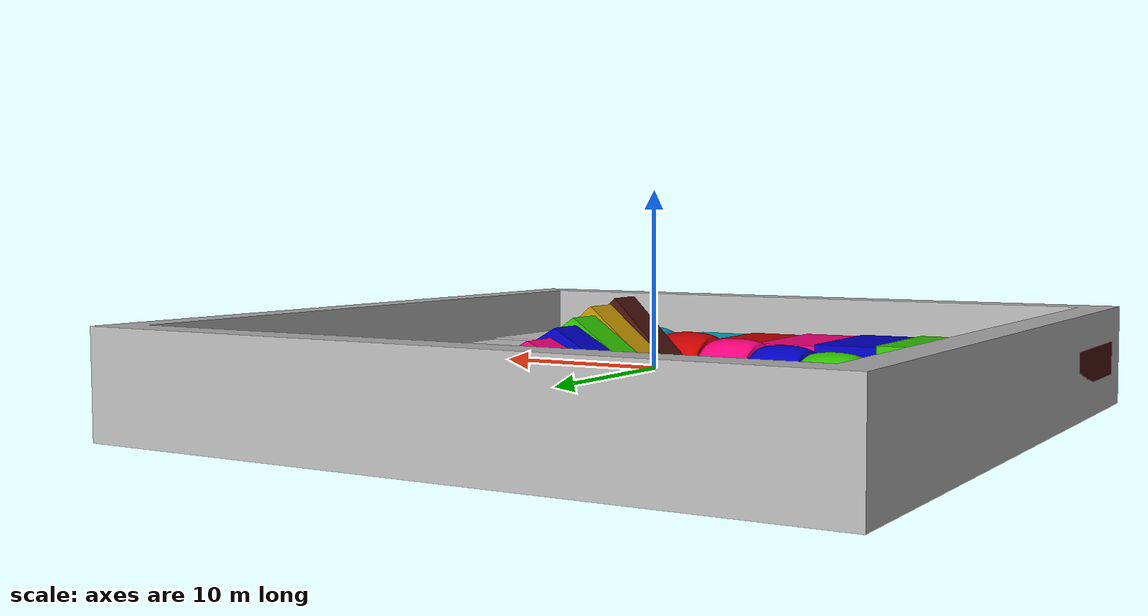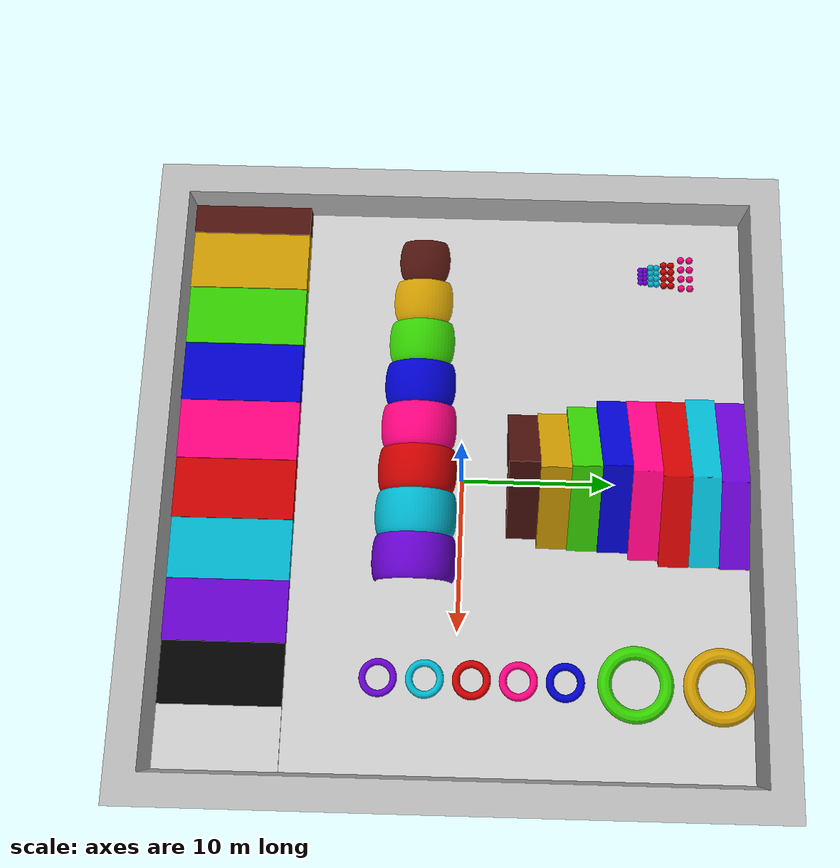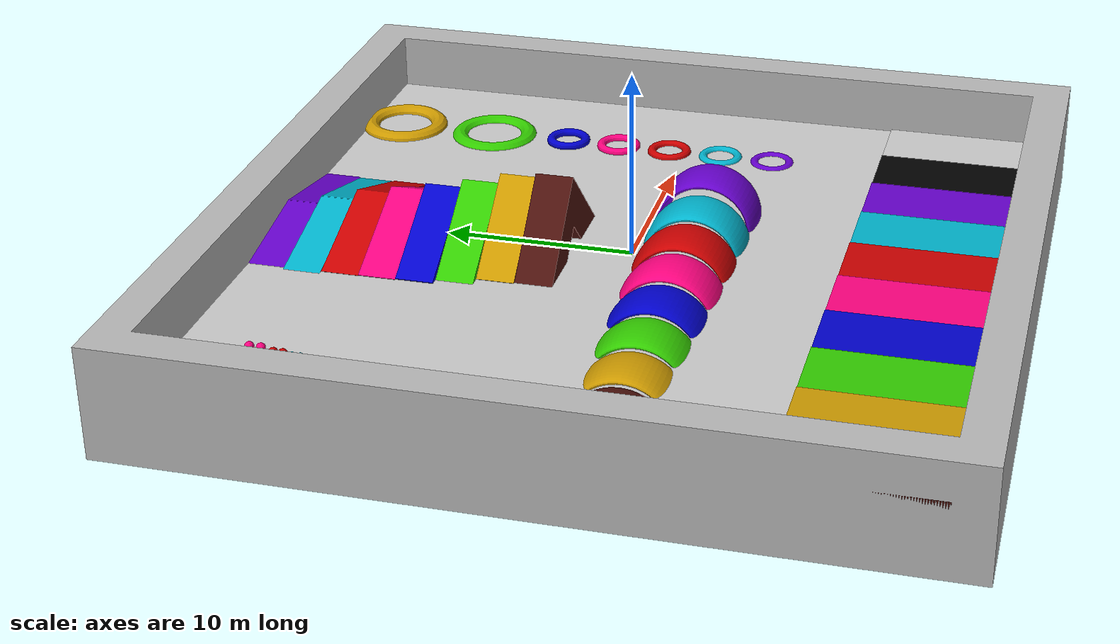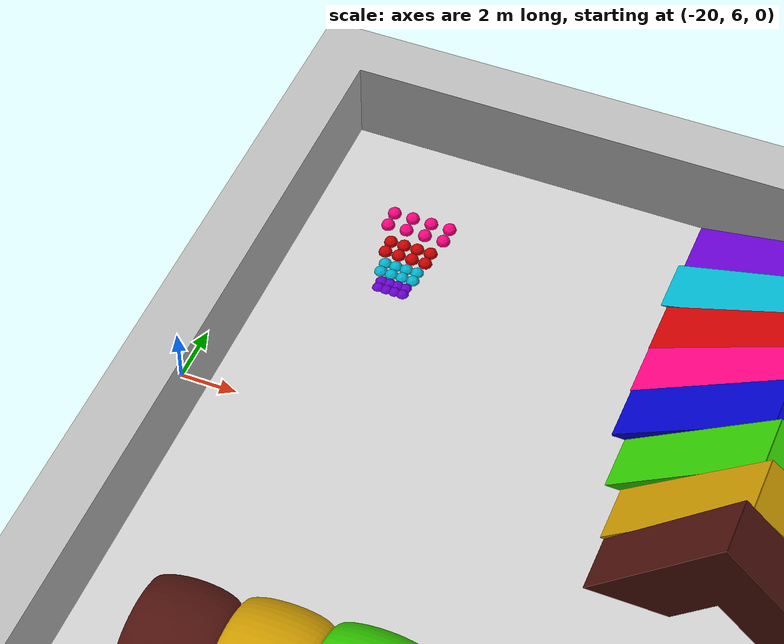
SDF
<?xml version="1.0" ?>
<sdf version="1.6">
  <model name="roboskel_playground">
    <static>true</static>

    <link name="slope45">
      <collision name="collision">
        <pose>0 0 0.01 0 0 0</pose>
        <geometry>
          <mesh>
            <uri>model://roboskel_playground/meshes/slope45.dae</uri>
          </mesh>
        </geometry>
        <surface>
          <friction>
            <ode>
              <mu>1.0</mu>
              <mu2>1.0</mu2>
            </ode>
          </friction>
          <contact>
            <ode>
              <kp>10000000.0</kp>
              <kd>1.0</kd>
              <min_depth>0.001</min_depth>
              <max_vel>0.1</max_vel>
            </ode>
          </contact>
        </surface>
      </collision>
      <visual name="visual">
        <cast_shadows>false</cast_shadows>
        <pose>0 0 0.01 0 0 0</pose>
        <geometry>
          <mesh>
            <uri>model://roboskel_playground/meshes/slope45.dae</uri>
          </mesh>
        </geometry>
        <material>
          <ambient>0.3 0.07 0.05 1</ambient>
          <diffuse>0.3 0.07 0.05 1</diffuse>
          <specular>0.1 0.1 0.1 1</specular>
          <emissive>0 0 0 0</emissive>
        </material>
      </visual>
    </link>

    <link name="slope40">
      <collision name="collision">
        <pose>0 0 0.01 0 0 0</pose>
        <geometry>
          <mesh>
            <uri>model://roboskel_playground/meshes/slope40.dae</uri>
          </mesh>
        </geometry>
        <surface>
          <friction>
            <ode>
              <mu>1.0</mu>
              <mu2>1.0</mu2>
            </ode>
          </friction>
          <contact>
            <ode>
              <kp>10000000.0</kp>
              <kd>1.0</kd>
              <min_depth>0.001</min_depth>
              <max_vel>0.1</max_vel>
            </ode>
          </contact>
        </surface>
      </collision>
      <visual name="visual">
        <cast_shadows>false</cast_shadows>
        <pose>0 0 0.01 0 0 0</pose>
        <geometry>
          <mesh>
            <uri>model://roboskel_playground/meshes/slope40.dae</uri>
          </mesh>
        </geometry>
        <material>
          <ambient>0.8 0.6 0 1</ambient>
          <diffuse>0.8 0.6 0 1</diffuse>
          <specular>0.1 0.1 0.1 1</specular>
          <emissive>0 0 0 0</emissive>
        </material>
      </visual>
    </link>

    <link name="slope35">
      <collision name="collision">
        <pose>0 0 0.01 0 0 0</pose>
        <geometry>
          <mesh>
            <uri>model://roboskel_playground/meshes/slope35.dae</uri>
          </mesh>
        </geometry>
        <surface>
          <friction>
            <ode>
              <mu>1.0</mu>
              <mu2>1.0</mu2>
            </ode>
          </friction>
          <contact>
            <ode>
              <kp>10000000.0</kp>
              <kd>1.0</kd>
              <min_depth>0.001</min_depth>
              <max_vel>0.1</max_vel>
            </ode>
          </contact>
        </surface>
      </collision>
      <visual name="visual">
        <cast_shadows>false</cast_shadows>
        <pose>0 0 0.01 0 0 0</pose>
        <geometry>
          <mesh>
            <uri>model://roboskel_playground/meshes/slope35.dae</uri>
          </mesh>
        </geometry>
        <material>
          <ambient>0.2 0.8 0 1</ambient>
          <diffuse>0.2 0.8 0 1</diffuse>
          <specular>0.1 0.1 0.1 1</specular>
          <emissive>0 0 0 0</emissive>
        </material>
      </visual>
    </link>

    <link name="slope30">
      <collision name="collision">
        <pose>0 0 0.01 0 0 0</pose>
        <geometry>
          <mesh>
            <uri>model://roboskel_playground/meshes/slope30.dae</uri>
          </mesh>
        </geometry>
        <surface>
          <friction>
            <ode>
              <mu>1.0</mu>
              <mu2>1.0</mu2>
            </ode>
          </friction>
          <contact>
            <ode>
              <kp>10000000.0</kp>
              <kd>1.0</kd>
              <min_depth>0.001</min_depth>
              <max_vel>0.1</max_vel>
            </ode>
          </contact>
        </surface>
      </collision>
      <visual name="visual">
        <cast_shadows>false</cast_shadows>
        <pose>0 0 0.01 0 0 0</pose>
        <geometry>
          <mesh>
            <uri>model://roboskel_playground/meshes/slope30.dae</uri>
          </mesh>
        </geometry>
        <material>
          <ambient>0 0 0.8 1</ambient>
          <diffuse>0 0 0.8 1</diffuse>
          <specular>0.1 0.1 0.1 1</specular>
          <emissive>0 0 0 0</emissive>
        </material>
      </visual>
    </link>

    <link name="slope25">
      <collision name="collision">
        <pose>0 0 0.01 0 0 0</pose>
        <geometry>
          <mesh>
            <uri>model://roboskel_playground/meshes/slope25.dae</uri>
          </mesh>
        </geometry>
        <surface>
          <friction>
            <ode>
              <mu>1.0</mu>
              <mu2>1.0</mu2>
            </ode>
          </friction>
          <contact>
            <ode>
              <kp>10000000.0</kp>
              <kd>1.0</kd>
              <min_depth>0.001</min_depth>
              <max_vel>0.1</max_vel>
            </ode>
          </contact>
        </surface>
      </collision>
      <visual name="visual">
        <cast_shadows>false</cast_shadows>
        <pose>0 0 0.01 0 0 0</pose>
        <geometry>
          <mesh>
            <uri>model://roboskel_playground/meshes/slope25.dae</uri>
          </mesh>
        </geometry>
        <material>
          <ambient>1 0 0.5 1</ambient>
          <diffuse>1 0 0.5 1</diffuse>
          <specular>0.1 0.1 0.1 1</specular>
          <emissive>0 0 0 0</emissive>
        </material>
      </visual>
    </link>

    <link name="slope20">
      <collision name="collision">
        <pose>0 0 0.01 0 0 0</pose>
        <geometry>
          <mesh>
            <uri>model://roboskel_playground/meshes/slope20.dae</uri>
          </mesh>
        </geometry>
        <surface>
          <friction>
            <ode>
              <mu>1.0</mu>
              <mu2>1.0</mu2>
            </ode>
          </friction>
          <contact>
            <ode>
              <kp>10000000.0</kp>
              <kd>1.0</kd>
              <min_depth>0.001</min_depth>
              <max_vel>0.1</max_vel>
            </ode>
          </contact>
        </surface>
      </collision>
      <visual name="visual">
        <cast_shadows>false</cast_shadows>
        <pose>0 0 0.01 0 0 0</pose>
        <geometry>
          <mesh>
            <uri>model://roboskel_playground/meshes/slope20.dae</uri>
          </mesh>
        </geometry>
        <material>
          <ambient>0.8 0 0 1</ambient>
          <diffuse>0.8 0 0 1</diffuse>
          <specular>0.1 0.1 0.1 1</specular>
          <emissive>0 0 0 0</emissive>
        </material>
      </visual>
    </link>

    <link name="slope15">
      <collision name="collision">
        <pose>0 0 0.01 0 0 0</pose>
        <geometry>
          <mesh>
            <uri>model://roboskel_playground/meshes/slope15.dae</uri>
          </mesh>
        </geometry>
        <surface>
          <friction>
            <ode>
              <mu>1.0</mu>
              <mu2>1.0</mu2>
            </ode>
          </friction>
          <contact>
            <ode>
              <kp>10000000.0</kp>
              <kd>1.0</kd>
              <min_depth>0.001</min_depth>
              <max_vel>0.1</max_vel>
            </ode>
          </contact>
        </surface>
      </collision>
      <visual name="visual">
        <cast_shadows>false</cast_shadows>
        <pose>0 0 0.01 0 0 0</pose>
        <geometry>
          <mesh>
            <uri>model://roboskel_playground/meshes/slope15.dae</uri>
          </mesh>
        </geometry>
        <material>
          <ambient>0 0.7 0.8 1</ambient>
          <diffuse>0 0.7 0.8 1</diffuse>
          <specular>0.1 0.1 0.1 1</specular>
          <emissive>0 0 0 0</emissive>
        </material>
      </visual>
    </link>

    <link name="slope10">
      <collision name="collision">
        <pose>0 0 0.01 0 0 0</pose>
        <geometry>
          <mesh>
            <uri>model://roboskel_playground/meshes/slope10.dae</uri>
          </mesh>
        </geometry>
        <surface>
          <friction>
            <ode>
              <mu>1.0</mu>
              <mu2>1.0</mu2>
            </ode>
          </friction>
          <contact>
            <ode>
              <kp>10000000.0</kp>
              <kd>1.0</kd>
              <min_depth>0.001</min_depth>
              <max_vel>0.1</max_vel>
            </ode>
          </contact>
        </surface>
      </collision>
      <visual name="visual">
        <cast_shadows>false</cast_shadows>
        <pose>0 0 0.01 0 0 0</pose>
        <geometry>
          <mesh>
            <uri>model://roboskel_playground/meshes/slope10.dae</uri>
          </mesh>
        </geometry>
        <material>
          <ambient>0.4 0 0.8 1</ambient>
          <diffuse>0.4 0 0.8 1</diffuse>
          <specular>0.1 0.1 0.1 1</specular>
          <emissive>0 0 0 0</emissive>
        </material>
      </visual>
    </link>

    <link name="step10">
      <collision name="collision">
        <pose>0 0 0.01 0 0 0</pose>
        <geometry>
          <mesh>
            <uri>model://roboskel_playground/meshes/step10.dae</uri>
          </mesh>
        </geometry>
        <surface>
          <friction>
            <ode>
              <mu>1.0</mu>
              <mu2>1.0</mu2>
            </ode>
          </friction>
          <contact>
            <ode>
              <kp>10000000.0</kp>
              <kd>1.0</kd>
              <min_depth>0.001</min_depth>
              <max_vel>0.1</max_vel>
            </ode>
          </contact>
        </surface>
      </collision>
      <visual name="visual">
        <cast_shadows>false</cast_shadows>
        <pose>0 0 0.01 0 0 0</pose>
        <geometry>
          <mesh>
            <uri>model://roboskel_playground/meshes/step10.dae</uri>
          </mesh>
        </geometry>
        <material>
          <ambient>0.3 0.07 0.05 1</ambient>
          <diffuse>0.3 0.07 0.05 1</diffuse>
          <specular>0.1 0.1 0.1 1</specular>
          <emissive>0 0 0 0</emissive>
        </material>
      </visual>
    </link>

    <link name="step9">
      <collision name="collision">
        <pose>0 0 0.01 0 0 0</pose>
        <geometry>
          <mesh>
            <uri>model://roboskel_playground/meshes/step9.dae</uri>
          </mesh>
        </geometry>
        <surface>
          <friction>
            <ode>
              <mu>1.0</mu>
              <mu2>1.0</mu2>
            </ode>
          </friction>
          <contact>
            <ode>
              <kp>10000000.0</kp>
              <kd>1.0</kd>
              <min_depth>0.001</min_depth>
              <max_vel>0.1</max_vel>
            </ode>
          </contact>
        </surface>
      </collision>
      <visual name="visual">
        <cast_shadows>false</cast_shadows>
        <pose>0 0 0.01 0 0 0</pose>
        <geometry>
          <mesh>
            <uri>model://roboskel_playground/meshes/step9.dae</uri>
          </mesh>
        </geometry>
        <material>
          <ambient>0.8 0.6 0 1</ambient>
          <diffuse>0.8 0.6 0 1</diffuse>
          <specular>0.1 0.1 0.1 1</specular>
          <emissive>0 0 0 0</emissive>
        </material>
      </visual>
    </link>

    <link name="step8">
      <collision name="collision">
        <pose>0 0 0.01 0 0 0</pose>
        <geometry>
          <mesh>
            <uri>model://roboskel_playground/meshes/step8.dae</uri>
          </mesh>
        </geometry>
        <surface>
          <friction>
            <ode>
              <mu>1.0</mu>
              <mu2>1.0</mu2>
            </ode>
          </friction>
          <contact>
            <ode>
              <kp>10000000.0</kp>
              <kd>1.0</kd>
              <min_depth>0.001</min_depth>
              <max_vel>0.1</max_vel>
            </ode>
          </contact>
        </surface>
      </collision>
      <visual name="visual">
        <cast_shadows>false</cast_shadows>
        <pose>0 0 0.01 0 0 0</pose>
        <geometry>
          <mesh>
            <uri>model://roboskel_playground/meshes/step8.dae</uri>
          </mesh>
        </geometry>
        <material>
          <ambient>0.2 0.8 0 1</ambient>
          <diffuse>0.2 0.8 0 1</diffuse>
          <specular>0.1 0.1 0.1 1</specular>
          <emissive>0 0 0 0</emissive>
        </material>
      </visual>
    </link>

    <link name="step7">
      <collision name="collision">
        <pose>0 0 0.01 0 0 0</pose>
        <geometry>
          <mesh>
            <uri>model://roboskel_playground/meshes/step7.dae</uri>
          </mesh>
        </geometry>
        <surface>
          <friction>
            <ode>
              <mu>1.0</mu>
              <mu2>1.0</mu2>
            </ode>
          </friction>
          <contact>
            <ode>
              <kp>10000000.0</kp>
              <kd>1.0</kd>
              <min_depth>0.001</min_depth>
              <max_vel>0.1</max_vel>
            </ode>
          </contact>
        </surface>
      </collision>
      <visual name="visual">
        <cast_shadows>false</cast_shadows>
        <pose>0 0 0.01 0 0 0</pose>
        <geometry>
          <mesh>
            <uri>model://roboskel_playground/meshes/step7.dae</uri>
          </mesh>
        </geometry>
        <material>
          <ambient>0 0 0.8 1</ambient>
          <diffuse>0 0 0.8 1</diffuse>
          <specular>0.1 0.1 0.1 1</specular>
          <emissive>0 0 0 0</emissive>
        </material>
      </visual>
    </link>

    <link name="step6">
      <collision name="collision">
        <pose>0 0 0.01 0 0 0</pose>
        <geometry>
          <mesh>
            <uri>model://roboskel_playground/meshes/step6.dae</uri>
          </mesh>
        </geometry>
        <surface>
          <friction>
            <ode>
              <mu>1.0</mu>
              <mu2>1.0</mu2>
            </ode>
          </friction>
          <contact>
            <ode>
              <kp>10000000.0</kp>
              <kd>1.0</kd>
              <min_depth>0.001</min_depth>
              <max_vel>0.1</max_vel>
            </ode>
          </contact>
        </surface>
      </collision>
      <visual name="visual">
        <cast_shadows>false</cast_shadows>
        <pose>0 0 0.01 0 0 0</pose>
        <geometry>
          <mesh>
            <uri>model://roboskel_playground/meshes/step6.dae</uri>
          </mesh>
        </geometry>
        <material>
          <ambient>1 0 0.5 1</ambient>
          <diffuse>1 0 0.5 1</diffuse>
          <specular>0.1 0.1 0.1 1</specular>
          <emissive>0 0 0 0</emissive>
        </material>
      </visual>
    </link>

    <link name="step5">
      <collision name="collision">
        <pose>0 0 0.01 0 0 0</pose>
        <geometry>
          <mesh>
            <uri>model://roboskel_playground/meshes/step5.dae</uri>
          </mesh>
        </geometry>
        <surface>
          <friction>
            <ode>
              <mu>1.0</mu>
              <mu2>1.0</mu2>
            </ode>
          </friction>
          <contact>
            <ode>
              <kp>10000000.0</kp>
              <kd>1.0</kd>
              <min_depth>0.001</min_depth>
              <max_vel>0.1</max_vel>
            </ode>
          </contact>
        </surface>
      </collision>
      <visual name="visual">
        <cast_shadows>false</cast_shadows>
        <pose>0 0 0.01 0 0 0</pose>
        <geometry>
          <mesh>
            <uri>model://roboskel_playground/meshes/step5.dae</uri>
          </mesh>
        </geometry>
        <material>
          <ambient>0.8 0 0 1</ambient>
          <diffuse>0.8 0 0 1</diffuse>
          <specular>0.1 0.1 0.1 1</specular>
          <emissive>0 0 0 0</emissive>
        </material>
      </visual>
    </link>

    <link name="step4">
      <collision name="collision">
        <pose>0 0 0.01 0 0 0</pose>
        <geometry>
          <mesh>
            <uri>model://roboskel_playground/meshes/step4.dae</uri>
          </mesh>
        </geometry>
        <surface>
          <friction>
            <ode>
              <mu>1.0</mu>
              <mu2>1.0</mu2>
            </ode>
          </friction>
          <contact>
            <ode>
              <kp>10000000.0</kp>
              <kd>1.0</kd>
              <min_depth>0.001</min_depth>
              <max_vel>0.1</max_vel>
            </ode>
          </contact>
        </surface>
      </collision>
      <visual name="visual">
        <cast_shadows>false</cast_shadows>
        <pose>0 0 0.01 0 0 0</pose>
        <geometry>
          <mesh>
            <uri>model://roboskel_playground/meshes/step4.dae</uri>
          </mesh>
        </geometry>
        <material>
          <ambient>0 0.7 0.8 1</ambient>
          <diffuse>0 0.7 0.8 1</diffuse>
          <specular>0.1 0.1 0.1 1</specular>
          <emissive>0 0 0 0</emissive>
        </material>
      </visual>
    </link>

    <link name="step3">
      <collision name="collision">
        <pose>0 0 0.01 0 0 0</pose>
        <geometry>
          <mesh>
            <uri>model://roboskel_playground/meshes/step3.dae</uri>
          </mesh>
        </geometry>
        <surface>
          <friction>
            <ode>
              <mu>1.0</mu>
              <mu2>1.0</mu2>
            </ode>
          </friction>
          <contact>
            <ode>
              <kp>10000000.0</kp>
              <kd>1.0</kd>
              <min_depth>0.001</min_depth>
              <max_vel>0.1</max_vel>
            </ode>
          </contact>
        </surface>
      </collision>
      <visual name="visual">
        <cast_shadows>false</cast_shadows>
        <pose>0 0 0.01 0 0 0</pose>
        <geometry>
          <mesh>
            <uri>model://roboskel_playground/meshes/step3.dae</uri>
          </mesh>
        </geometry>
        <material>
          <ambient>0.4 0 0.8 1</ambient>
          <diffuse>0.4 0 0.8 1</diffuse>
          <specular>0.1 0.1 0.1 1</specular>
          <emissive>0 0 0 0</emissive>
        </material>
      </visual>
    </link>

    <link name="step2">
      <collision name="collision">
        <pose>0 0 0.01 0 0 0</pose>
        <geometry>
          <mesh>
            <uri>model://roboskel_playground/meshes/step2.dae</uri>
          </mesh>
        </geometry>
        <surface>
          <friction>
            <ode>
              <mu>1.0</mu>
              <mu2>1.0</mu2>
            </ode>
          </friction>
          <contact>
            <ode>
              <kp>10000000.0</kp>
              <kd>1.0</kd>
              <min_depth>0.001</min_depth>
              <max_vel>0.1</max_vel>
            </ode>
          </contact>
        </surface>
      </collision>
      <visual name="visual">
        <cast_shadows>false</cast_shadows>
        <pose>0 0 0.01 0 0 0</pose>
        <geometry>
          <mesh>
            <uri>model://roboskel_playground/meshes/step2.dae</uri>
          </mesh>
        </geometry>
        <material>
          <ambient>0 0 0 1</ambient>
          <diffuse>0 0 0 1</diffuse>
          <specular>0.1 0.1 0.1 1</specular>
          <emissive>0 0 0 0</emissive>
        </material>
      </visual>
    </link>

    <link name="step1">
      <collision name="collision">
        <pose>0 0 0.01 0 0 0</pose>
        <geometry>
          <mesh>
            <uri>model://roboskel_playground/meshes/step1.dae</uri>
          </mesh>
        </geometry>
        <surface>
          <friction>
            <ode>
              <mu>1.0</mu>
              <mu2>1.0</mu2>
            </ode>
          </friction>
          <contact>
            <ode>
              <kp>10000000.0</kp>
              <kd>1.0</kd>
              <min_depth>0.001</min_depth>
              <max_vel>0.1</max_vel>
            </ode>
          </contact>
        </surface>
      </collision>
      <visual name="visual">
        <cast_shadows>false</cast_shadows>
        <pose>0 0 0.01 0 0 0</pose>
        <geometry>
          <mesh>
            <uri>model://roboskel_playground/meshes/step1.dae</uri>
          </mesh>
        </geometry>
        <material>
          <ambient>0.8 0.8 0.8 1</ambient>
          <diffuse>0.8 0.8 0.8 1</diffuse>
          <specular>0.1 0.1 0.1 1</specular>
          <emissive>0 0 0 0</emissive>
        </material>
      </visual>
    </link>

    <link name="small_ring1">
      <collision name="collision">
        <pose>0 0 0.01 0 0 0</pose>
        <geometry>
          <mesh>
            <uri>model://roboskel_playground/meshes/small_ring1.dae</uri>
          </mesh>
        </geometry>
        <surface>
          <friction>
            <ode>
              <mu>1.0</mu>
              <mu2>1.0</mu2>
            </ode>
          </friction>
          <contact>
            <ode>
              <kp>10000000.0</kp>
              <kd>1.0</kd>
              <min_depth>0.001</min_depth>
              <max_vel>0.1</max_vel>
            </ode>
          </contact>
        </surface>
      </collision>
      <visual name="visual">
        <cast_shadows>false</cast_shadows>
        <pose>0 0 0.01 0 0 0</pose>
        <geometry>
          <mesh>
            <uri>model://roboskel_playground/meshes/small_ring1.dae</uri>
          </mesh>
        </geometry>
        <material>
          <ambient>0.4 0 0.8 1</ambient>
          <diffuse>0.4 0 0.8 1</diffuse>
          <specular>0.1 0.1 0.1 1</specular>
          <emissive>0 0 0 0</emissive>
        </material>
      </visual>
    </link>

    <link name="small_ring2">
      <collision name="collision">
        <pose>0 0 0.01 0 0 0</pose>
        <geometry>
          <mesh>
            <uri>model://roboskel_playground/meshes/small_ring2.dae</uri>
          </mesh>
        </geometry>
        <surface>
          <friction>
            <ode>
              <mu>1.0</mu>
              <mu2>1.0</mu2>
            </ode>
          </friction>
          <contact>
            <ode>
              <kp>10000000.0</kp>
              <kd>1.0</kd>
              <min_depth>0.001</min_depth>
              <max_vel>0.1</max_vel>
            </ode>
          </contact>
        </surface>
      </collision>
      <visual name="visual">
        <cast_shadows>false</cast_shadows>
        <pose>0 0 0.01 0 0 0</pose>
        <geometry>
          <mesh>
            <uri>model://roboskel_playground/meshes/small_ring2.dae</uri>
          </mesh>
        </geometry>
        <material>
          <ambient>0 0.7 0.8 1</ambient>
          <diffuse>0 0.7 0.8 1</diffuse>
          <specular>0.1 0.1 0.1 1</specular>
          <emissive>0 0 0 0</emissive>
        </material>
      </visual>
    </link>

    <link name="small_ring3">
      <collision name="collision">
        <pose>0 0 0.01 0 0 0</pose>
        <geometry>
          <mesh>
            <uri>model://roboskel_playground/meshes/small_ring3.dae</uri>
          </mesh>
        </geometry>
        <surface>
          <friction>
            <ode>
              <mu>1.0</mu>
              <mu2>1.0</mu2>
            </ode>
          </friction>
          <contact>
            <ode>
              <kp>10000000.0</kp>
              <kd>1.0</kd>
              <min_depth>0.001</min_depth>
              <max_vel>0.1</max_vel>
            </ode>
          </contact>
        </surface>
      </collision>
      <visual name="visual">
        <cast_shadows>false</cast_shadows>
        <pose>0 0 0.01 0 0 0</pose>
        <geometry>
          <mesh>
            <uri>model://roboskel_playground/meshes/small_ring3.dae</uri>
          </mesh>
        </geometry>
        <material>
          <ambient>0.8 0 0 1</ambient>
          <diffuse>0.8 0 0 1</diffuse>
          <specular>0.1 0.1 0.1 1</specular>
          <emissive>0 0 0 0</emissive>
        </material>
      </visual>
    </link>

    <link name="small_ring4">
      <collision name="collision">
        <pose>0 0 0.01 0 0 0</pose>
        <geometry>
          <mesh>
            <uri>model://roboskel_playground/meshes/small_ring4.dae</uri>
          </mesh>
        </geometry>
        <surface>
          <friction>
            <ode>
              <mu>1.0</mu>
              <mu2>1.0</mu2>
            </ode>
          </friction>
          <contact>
            <ode>
              <kp>10000000.0</kp>
              <kd>1.0</kd>
              <min_depth>0.001</min_depth>
              <max_vel>0.1</max_vel>
            </ode>
          </contact>
        </surface>
      </collision>
      <visual name="visual">
        <cast_shadows>false</cast_shadows>
        <pose>0 0 0.01 0 0 0</pose>
        <geometry>
          <mesh>
            <uri>model://roboskel_playground/meshes/small_ring4.dae</uri>
          </mesh>
        </geometry>
        <material>
          <ambient>1 0 0.5 1</ambient>
          <diffuse>1 0 0.5 1</diffuse>
          <specular>0.1 0.1 0.1 1</specular>
          <emissive>0 0 0 0</emissive>
        </material>
      </visual>
    </link>

    <link name="small_ring5">
      <collision name="collision">
        <pose>0 0 0.01 0 0 0</pose>
        <geometry>
          <mesh>
            <uri>model://roboskel_playground/meshes/small_ring5.dae</uri>
          </mesh>
        </geometry>
        <surface>
          <friction>
            <ode>
              <mu>1.0</mu>
              <mu2>1.0</mu2>
            </ode>
          </friction>
          <contact>
            <ode>
              <kp>10000000.0</kp>
              <kd>1.0</kd>
              <min_depth>0.001</min_depth>
              <max_vel>0.1</max_vel>
            </ode>
          </contact>
        </surface>
      </collision>
      <visual name="visual">
        <cast_shadows>false</cast_shadows>
        <pose>0 0 0.01 0 0 0</pose>
        <geometry>
          <mesh>
            <uri>model://roboskel_playground/meshes/small_ring5.dae</uri>
          </mesh>
        </geometry>
        <material>
          <ambient>0 0 0.8 1</ambient>
          <diffuse>0 0 0.8 1</diffuse>
          <specular>0.1 0.1 0.1 1</specular>
          <emissive>0 0 0 0</emissive>
        </material>
      </visual>
    </link>

    <link name="big_ring1">
      <collision name="collision">
        <pose>0 0 0.01 0 0 0</pose>
        <geometry>
          <mesh>
            <uri>model://roboskel_playground/meshes/big_ring1.dae</uri>
          </mesh>
        </geometry>
        <surface>
          <friction>
            <ode>
              <mu>1.0</mu>
              <mu2>1.0</mu2>
            </ode>
          </friction>
          <contact>
            <ode>
              <kp>10000000.0</kp>
              <kd>1.0</kd>
              <min_depth>0.001</min_depth>
              <max_vel>0.1</max_vel>
            </ode>
          </contact>
        </surface>
      </collision>
      <visual name="visual">
        <cast_shadows>false</cast_shadows>
        <pose>0 0 0.01 0 0 0</pose>
        <geometry>
          <mesh>
            <uri>model://roboskel_playground/meshes/big_ring1.dae</uri>
          </mesh>
        </geometry>
        <material>
          <ambient>0.2 0.8 0 1</ambient>
          <diffuse>0.2 0.8 0 1</diffuse>
          <specular>0.1 0.1 0.1 1</specular>
          <emissive>0 0 0 0</emissive>
        </material>
      </visual>
    </link>

    <link name="big_ring2">
      <collision name="collision">
        <pose>0 0 0.01 0 0 0</pose>
        <geometry>
          <mesh>
            <uri>model://roboskel_playground/meshes/big_ring2.dae</uri>
          </mesh>
        </geometry>
        <surface>
          <friction>
            <ode>
              <mu>1.0</mu>
              <mu2>1.0</mu2>
            </ode>
          </friction>
          <contact>
            <ode>
              <kp>10000000.0</kp>
              <kd>1.0</kd>
              <min_depth>0.001</min_depth>
              <max_vel>0.1</max_vel>
            </ode>
          </contact>
        </surface>
      </collision>
      <visual name="visual">
        <cast_shadows>false</cast_shadows>
        <pose>0 0 0.01 0 0 0</pose>
        <geometry>
          <mesh>
            <uri>model://roboskel_playground/meshes/big_ring2.dae</uri>
          </mesh>
        </geometry>
        <material>
          <ambient>0.8 0.6 0 1</ambient>
          <diffuse>0.8 0.6 0 1</diffuse>
          <specular>0.1 0.1 0.1 1</specular>
          <emissive>0 0 0 0</emissive>
        </material>
      </visual>
    </link>

    <link name="bigger_rock1">
      <collision name="collision">
        <pose>0 0.7 0.05 0 0 0</pose>
        <geometry>
          <mesh>
            <uri>model://roboskel_playground/meshes/rock.dae</uri>
          </mesh>
        </geometry>
        <surface>
          <friction>
            <ode>
              <mu>1.0</mu>
              <mu2>1.0</mu2>
            </ode>
          </friction>
          <contact>
            <ode>
              <kp>10000000.0</kp>
              <kd>1.0</kd>
              <min_depth>0.001</min_depth>
              <max_vel>0.1</max_vel>
            </ode>
          </contact>
        </surface>
      </collision>
      <visual name="visual">
        <cast_shadows>false</cast_shadows>
        <pose>0 0.7 0.05 0 0 0</pose>
        <geometry>
          <mesh>
            <uri>model://roboskel_playground/meshes/rock.dae</uri>
          </mesh>
        </geometry>
        <material>
          <ambient>1 0 0.5 1</ambient>
          <diffuse>1 0 0.5 1</diffuse>
          <specular>0.1 0.1 0.1 1</specular>
          <emissive>0 0 0 0</emissive>
        </material>
      </visual>
    </link>

    <link name="bigger_rock2">
      <collision name="collision">
        <pose>0.7 0.7 0.05 0 0 0</pose>
        <geometry>
          <mesh>
            <uri>model://roboskel_playground/meshes/rock.dae</uri>
          </mesh>
        </geometry>
        <surface>
          <friction>
            <ode>
              <mu>1.0</mu>
              <mu2>1.0</mu2>
            </ode>
          </friction>
          <contact>
            <ode>
              <kp>10000000.0</kp>
              <kd>1.0</kd>
              <min_depth>0.001</min_depth>
              <max_vel>0.1</max_vel>
            </ode>
          </contact>
        </surface>
      </collision>
      <visual name="visual">
        <cast_shadows>false</cast_shadows>
        <pose>0.7 0.7 0.05 0 0 0</pose>
        <geometry>
          <mesh>
            <uri>model://roboskel_playground/meshes/rock.dae</uri>
          </mesh>
        </geometry>
        <material>
          <ambient>1 0 0.5 1</ambient>
          <diffuse>1 0 0.5 1</diffuse>
          <specular>0.1 0.1 0.1 1</specular>
          <emissive>0 0 0 0</emissive>
        </material>
      </visual>
    </link>

    <link name="bigger_rock3">
      <collision name="collision">
        <pose>-0.7 0.7 0.05 0 0 0</pose>
        <geometry>
          <mesh>
            <uri>model://roboskel_playground/meshes/rock.dae</uri>
          </mesh>
        </geometry>
        <surface>
          <friction>
            <ode>
              <mu>1.0</mu>
              <mu2>1.0</mu2>
            </ode>
          </friction>
          <contact>
            <ode>
              <kp>10000000.0</kp>
              <kd>1.0</kd>
              <min_depth>0.001</min_depth>
              <max_vel>0.1</max_vel>
            </ode>
          </contact>
        </surface>
      </collision>
      <visual name="visual">
        <cast_shadows>false</cast_shadows>
        <pose>-0.7 0.7 0.05 0 0 0</pose>
        <geometry>
          <mesh>
            <uri>model://roboskel_playground/meshes/rock.dae</uri>
          </mesh>
        </geometry>
        <material>
          <ambient>1 0 0.5 1</ambient>
          <diffuse>1 0 0.5 1</diffuse>
          <specular>0.1 0.1 0.1 1</specular>
          <emissive>0 0 0 0</emissive>
        </material>
      </visual>
    </link>

    <link name="bigger_rock4">
      <collision name="collision">
        <pose>-1.4 0.7 0.05 0 0 0</pose>
        <geometry>
          <mesh>
            <uri>model://roboskel_playground/meshes/rock.dae</uri>
          </mesh>
        </geometry>
        <surface>
          <friction>
            <ode>
              <mu>1.0</mu>
              <mu2>1.0</mu2>
            </ode>
          </friction>
          <contact>
            <ode>
              <kp>10000000.0</kp>
              <kd>1.0</kd>
              <min_depth>0.001</min_depth>
              <max_vel>0.1</max_vel>
            </ode>
          </contact>
        </surface>
      </collision>
      <visual name="visual">
        <cast_shadows>false</cast_shadows>
        <pose>-1.4 0.7 0.05 0 0 0</pose>
        <geometry>
          <mesh>
            <uri>model://roboskel_playground/meshes/rock.dae</uri>
          </mesh>
        </geometry>
        <material>
          <ambient>1 0 0.5 1</ambient>
          <diffuse>1 0 0.5 1</diffuse>
          <specular>0.1 0.1 0.1 1</specular>
          <emissive>0 0 0 0</emissive>
        </material>
      </visual>
    </link>

    <link name="bigger_rock5">
      <collision name="collision">
        <pose>0 1.3 0.05 0 0 0</pose>
        <geometry>
          <mesh>
            <uri>model://roboskel_playground/meshes/rock.dae</uri>
          </mesh>
        </geometry>
        <surface>
          <friction>
            <ode>
              <mu>1.0</mu>
              <mu2>1.0</mu2>
            </ode>
          </friction>
          <contact>
            <ode>
              <kp>10000000.0</kp>
              <kd>1.0</kd>
              <min_depth>0.001</min_depth>
              <max_vel>0.1</max_vel>
            </ode>
          </contact>
        </surface>
      </collision>
      <visual name="visual">
        <cast_shadows>false</cast_shadows>
        <pose>0 1.3 0.05 0 0 0</pose>
        <geometry>
          <mesh>
            <uri>model://roboskel_playground/meshes/rock.dae</uri>
          </mesh>
        </geometry>
        <material>
          <ambient>1 0 0.5 1</ambient>
          <diffuse>1 0 0.5 1</diffuse>
          <specular>0.1 0.1 0.1 1</specular>
          <emissive>0 0 0 0</emissive>
        </material>
      </visual>
    </link>

    <link name="bigger_rock6">
      <collision name="collision">
        <pose>0.7 1.3 0.05 0 0 0</pose>
        <geometry>
          <mesh>
            <uri>model://roboskel_playground/meshes/rock.dae</uri>
          </mesh>
        </geometry>
        <surface>
          <friction>
            <ode>
              <mu>1.0</mu>
              <mu2>1.0</mu2>
            </ode>
          </friction>
          <contact>
            <ode>
              <kp>10000000.0</kp>
              <kd>1.0</kd>
              <min_depth>0.001</min_depth>
              <max_vel>0.1</max_vel>
            </ode>
          </contact>
        </surface>
      </collision>
      <visual name="visual">
        <cast_shadows>false</cast_shadows>
        <pose>0.7 1.3 0.05 0 0 0</pose>
        <geometry>
          <mesh>
            <uri>model://roboskel_playground/meshes/rock.dae</uri>
          </mesh>
        </geometry>
        <material>
          <ambient>1 0 0.5 1</ambient>
          <diffuse>1 0 0.5 1</diffuse>
          <specular>0.1 0.1 0.1 1</specular>
          <emissive>0 0 0 0</emissive>
        </material>
      </visual>
    </link>

    <link name="bigger_rock7">
      <collision name="collision">
        <pose>-0.7 1.3 0.05 0 0 0</pose>
        <geometry>
          <mesh>
            <uri>model://roboskel_playground/meshes/rock.dae</uri>
          </mesh>
        </geometry>
        <surface>
          <friction>
            <ode>
              <mu>1.0</mu>
              <mu2>1.0</mu2>
            </ode>
          </friction>
          <contact>
            <ode>
              <kp>10000000.0</kp>
              <kd>1.0</kd>
              <min_depth>0.001</min_depth>
              <max_vel>0.1</max_vel>
            </ode>
          </contact>
        </surface>
      </collision>
      <visual name="visual">
        <cast_shadows>false</cast_shadows>
        <pose>-0.7 1.3 0.05 0 0 0</pose>
        <geometry>
          <mesh>
            <uri>model://roboskel_playground/meshes/rock.dae</uri>
          </mesh>
        </geometry>
        <material>
          <ambient>1 0 0.5 1</ambient>
          <diffuse>1 0 0.5 1</diffuse>
          <specular>0.1 0.1 0.1 1</specular>
          <emissive>0 0 0 0</emissive>
        </material>
      </visual>
    </link>

    <link name="bigger_rock8">
      <collision name="collision">
        <pose>-1.4 1.3 0.05 0 0 0</pose>
        <geometry>
          <mesh>
            <uri>model://roboskel_playground/meshes/rock.dae</uri>
          </mesh>
        </geometry>
        <surface>
          <friction>
            <ode>
              <mu>1.0</mu>
              <mu2>1.0</mu2>
            </ode>
          </friction>
          <contact>
            <ode>
              <kp>10000000.0</kp>
              <kd>1.0</kd>
              <min_depth>0.001</min_depth>
              <max_vel>0.1</max_vel>
            </ode>
          </contact>
        </surface>
      </collision>
      <visual name="visual">
        <cast_shadows>false</cast_shadows>
        <pose>-1.4 1.3 0.05 0 0 0</pose>
        <geometry>
          <mesh>
            <uri>model://roboskel_playground/meshes/rock.dae</uri>
          </mesh>
        </geometry>
        <material>
          <ambient>1 0 0.5 1</ambient>
          <diffuse>1 0 0.5 1</diffuse>
          <specular>0.1 0.1 0.1 1</specular>
          <emissive>0 0 0 0</emissive>
        </material>
      </visual>
    </link>

    <link name="big_rock1">
      <collision name="collision">
        <pose>0 0 0.01 0 0 0</pose>
        <geometry>
          <mesh>
            <uri>model://roboskel_playground/meshes/rock.dae</uri>
          </mesh>
        </geometry>
        <surface>
          <friction>
            <ode>
              <mu>1.0</mu>
              <mu2>1.0</mu2>
            </ode>
          </friction>
          <contact>
            <ode>
              <kp>10000000.0</kp>
              <kd>1.0</kd>
              <min_depth>0.001</min_depth>
              <max_vel>0.1</max_vel>
            </ode>
          </contact>
        </surface>
      </collision>
      <visual name="visual">
        <cast_shadows>false</cast_shadows>
        <pose>0 0 0.01 0 0 0</pose>
        <geometry>
          <mesh>
            <uri>model://roboskel_playground/meshes/rock.dae</uri>
          </mesh>
        </geometry>
        <material>
          <ambient>0.8 0 0 1</ambient>
          <diffuse>0.8 0 0 1</diffuse>
          <specular>0.1 0.1 0.1 1</specular>
          <emissive>0 0 0 0</emissive>
        </material>
      </visual>
    </link>

    <link name="big_rock2">
      <collision name="collision">
        <pose>0.5 0 0.01 0 0 0</pose>
        <geometry>
          <mesh>
            <uri>model://roboskel_playground/meshes/rock.dae</uri>
          </mesh>
        </geometry>
        <surface>
          <friction>
            <ode>
              <mu>1.0</mu>
              <mu2>1.0</mu2>
            </ode>
          </friction>
          <contact>
            <ode>
              <kp>10000000.0</kp>
              <kd>1.0</kd>
              <min_depth>0.001</min_depth>
              <max_vel>0.1</max_vel>
            </ode>
          </contact>
        </surface>
      </collision>
      <visual name="visual">
        <cast_shadows>false</cast_shadows>
        <pose>0.5 0 0.01 0 0 0</pose>
        <geometry>
          <mesh>
            <uri>model://roboskel_playground/meshes/rock.dae</uri>
          </mesh>
        </geometry>
        <material>
          <ambient>0.8 0 0 1</ambient>
          <diffuse>0.8 0 0 1</diffuse>
          <specular>0.1 0.1 0.1 1</specular>
          <emissive>0 0 0 0</emissive>
        </material>
      </visual>
    </link>

    <link name="big_rock3">
      <collision name="collision">
        <pose>-0.5 0 0.01 0 0 0</pose>
        <geometry>
          <mesh>
            <uri>model://roboskel_playground/meshes/rock.dae</uri>
          </mesh>
        </geometry>
        <surface>
          <friction>
            <ode>
              <mu>1.0</mu>
              <mu2>1.0</mu2>
            </ode>
          </friction>
          <contact>
            <ode>
              <kp>10000000.0</kp>
              <kd>1.0</kd>
              <min_depth>0.001</min_depth>
              <max_vel>0.1</max_vel>
            </ode>
          </contact>
        </surface>
      </collision>
      <visual name="visual">
        <cast_shadows>false</cast_shadows>
        <pose>-0.5 0 0.01 0 0 0</pose>
        <geometry>
          <mesh>
            <uri>model://roboskel_playground/meshes/rock.dae</uri>
          </mesh>
        </geometry>
        <material>
          <ambient>0.8 0 0 1</ambient>
          <diffuse>0.8 0 0 1</diffuse>
          <specular>0.1 0.1 0.1 1</specular>
          <emissive>0 0 0 0</emissive>
        </material>
      </visual>
    </link>

    <link name="big_rock4">
      <collision name="collision">
        <pose>-1 0 0.01 0 0 0</pose>
        <geometry>
          <mesh>
            <uri>model://roboskel_playground/meshes/rock.dae</uri>
          </mesh>
        </geometry>
        <surface>
          <friction>
            <ode>
              <mu>1.0</mu>
              <mu2>1.0</mu2>
            </ode>
          </friction>
          <contact>
            <ode>
              <kp>10000000.0</kp>
              <kd>1.0</kd>
              <min_depth>0.001</min_depth>
              <max_vel>0.1</max_vel>
            </ode>
          </contact>
        </surface>
      </collision>
      <visual name="visual">
        <cast_shadows>false</cast_shadows>
        <pose>-1 0 0.01 0 0 0</pose>
        <geometry>
          <mesh>
            <uri>model://roboskel_playground/meshes/rock.dae</uri>
          </mesh>
        </geometry>
        <material>
          <ambient>0.8 0 0 1</ambient>
          <diffuse>0.8 0 0 1</diffuse>
          <specular>0.1 0.1 0.1 1</specular>
          <emissive>0 0 0 0</emissive>
        </material>
      </visual>
    </link>

    <link name="big_rock5">
      <collision name="collision">
        <pose>0 -0.5 0.01 0 0 0</pose>
        <geometry>
          <mesh>
            <uri>model://roboskel_playground/meshes/rock.dae</uri>
          </mesh>
        </geometry>
        <surface>
          <friction>
            <ode>
              <mu>1.0</mu>
              <mu2>1.0</mu2>
            </ode>
          </friction>
          <contact>
            <ode>
              <kp>10000000.0</kp>
              <kd>1.0</kd>
              <min_depth>0.001</min_depth>
              <max_vel>0.1</max_vel>
            </ode>
          </contact>
        </surface>
      </collision>
      <visual name="visual">
        <cast_shadows>false</cast_shadows>
        <pose>0 -0.5 0.01 0 0 0</pose>
        <geometry>
          <mesh>
            <uri>model://roboskel_playground/meshes/rock.dae</uri>
          </mesh>
        </geometry>
        <material>
          <ambient>0.8 0 0 1</ambient>
          <diffuse>0.8 0 0 1</diffuse>
          <specular>0.1 0.1 0.1 1</specular>
          <emissive>0 0 0 0</emissive>
        </material>
      </visual>
    </link>

    <link name="big_rock6">
      <collision name="collision">
        <pose>0.5 -0.5 0.01 0 0 0</pose>
        <geometry>
          <mesh>
            <uri>model://roboskel_playground/meshes/rock.dae</uri>
          </mesh>
        </geometry>
        <surface>
          <friction>
            <ode>
              <mu>1.0</mu>
              <mu2>1.0</mu2>
            </ode>
          </friction>
          <contact>
            <ode>
              <kp>10000000.0</kp>
              <kd>1.0</kd>
              <min_depth>0.001</min_depth>
              <max_vel>0.1</max_vel>
            </ode>
          </contact>
        </surface>
      </collision>
      <visual name="visual">
        <cast_shadows>false</cast_shadows>
        <pose>0.5 -0.5 0.01 0 0 0</pose>
        <geometry>
          <mesh>
            <uri>model://roboskel_playground/meshes/rock.dae</uri>
          </mesh>
        </geometry>
        <material>
          <ambient>0.8 0 0 1</ambient>
          <diffuse>0.8 0 0 1</diffuse>
          <specular>0.1 0.1 0.1 1</specular>
          <emissive>0 0 0 0</emissive>
        </material>
      </visual>
    </link>

    <link name="big_rock7">
      <collision name="collision">
        <pose>-0.5 -0.5 0.01 0 0 0</pose>
        <geometry>
          <mesh>
            <uri>model://roboskel_playground/meshes/rock.dae</uri>
          </mesh>
        </geometry>
        <surface>
          <friction>
            <ode>
              <mu>1.0</mu>
              <mu2>1.0</mu2>
            </ode>
          </friction>
          <contact>
            <ode>
              <kp>10000000.0</kp>
              <kd>1.0</kd>
              <min_depth>0.001</min_depth>
              <max_vel>0.1</max_vel>
            </ode>
          </contact>
        </surface>
      </collision>
      <visual name="visual">
        <cast_shadows>false</cast_shadows>
        <pose>-0.5 -0.5 0.01 0 0 0</pose>
        <geometry>
          <mesh>
            <uri>model://roboskel_playground/meshes/rock.dae</uri>
          </mesh>
        </geometry>
        <material>
          <ambient>0.8 0 0 1</ambient>
          <diffuse>0.8 0 0 1</diffuse>
          <specular>0.1 0.1 0.1 1</specular>
          <emissive>0 0 0 0</emissive>
        </material>
      </visual>
    </link>

    <link name="big_rock8">
      <collision name="collision">
        <pose>-1 -0.5 0.01 0 0 0</pose>
        <geometry>
          <mesh>
            <uri>model://roboskel_playground/meshes/rock.dae</uri>
          </mesh>
        </geometry>
        <surface>
          <friction>
            <ode>
              <mu>1.0</mu>
              <mu2>1.0</mu2>
            </ode>
          </friction>
          <contact>
            <ode>
              <kp>10000000.0</kp>
              <kd>1.0</kd>
              <min_depth>0.001</min_depth>
              <max_vel>0.1</max_vel>
            </ode>
          </contact>
        </surface>
      </collision>
      <visual name="visual">
        <cast_shadows>false</cast_shadows>
        <pose>-1 -0.5 0.01 0 0 0</pose>
        <geometry>
          <mesh>
            <uri>model://roboskel_playground/meshes/rock.dae</uri>
          </mesh>
        </geometry>
        <material>
          <ambient>0.8 0 0 1</ambient>
          <diffuse>0.8 0 0 1</diffuse>
          <specular>0.1 0.1 0.1 1</specular>
          <emissive>0 0 0 0</emissive>
        </material>
      </visual>
    </link>

    <link name="mid_rock1">
      <collision name="collision">
        <pose>0 -1 -0.05 0 0 0</pose>
        <geometry>
          <mesh>
            <uri>model://roboskel_playground/meshes/rock.dae</uri>
          </mesh>
        </geometry>
        <surface>
          <friction>
            <ode>
              <mu>1.0</mu>
              <mu2>1.0</mu2>
            </ode>
          </friction>
          <contact>
            <ode>
              <kp>10000000.0</kp>
              <kd>1.0</kd>
              <min_depth>0.001</min_depth>
              <max_vel>0.1</max_vel>
            </ode>
          </contact>
        </surface>
      </collision>
      <visual name="visual">
        <cast_shadows>false</cast_shadows>
        <pose>0 -1 -0.05 0 0 0</pose>
        <geometry>
          <mesh>
            <uri>model://roboskel_playground/meshes/rock.dae</uri>
          </mesh>
        </geometry>
        <material>
          <ambient>0 0.7 0.8 1</ambient>
          <diffuse>0 0.7 0.8 1</diffuse>
          <specular>0.1 0.1 0.1 1</specular>
          <emissive>0 0 0 0</emissive>
        </material>
      </visual>
    </link>

    <link name="mid_rock2">
      <collision name="collision">
        <pose>0.4 -1 -0.05 0 0 0</pose>
        <geometry>
          <mesh>
            <uri>model://roboskel_playground/meshes/rock.dae</uri>
          </mesh>
        </geometry>
        <surface>
          <friction>
            <ode>
              <mu>1.0</mu>
              <mu2>1.0</mu2>
            </ode>
          </friction>
          <contact>
            <ode>
              <kp>10000000.0</kp>
              <kd>1.0</kd>
              <min_depth>0.001</min_depth>
              <max_vel>0.1</max_vel>
            </ode>
          </contact>
        </surface>
      </collision>
      <visual name="visual">
        <cast_shadows>false</cast_shadows>
        <pose>0.4 -1 -0.05 0 0 0</pose>
        <geometry>
          <mesh>
            <uri>model://roboskel_playground/meshes/rock.dae</uri>
          </mesh>
        </geometry>
        <material>
          <ambient>0 0.7 0.8 1</ambient>
          <diffuse>0 0.7 0.8 1</diffuse>
          <specular>0.1 0.1 0.1 1</specular>
          <emissive>0 0 0 0</emissive>
        </material>
      </visual>
    </link>

    <link name="mid_rock3">
      <collision name="collision">
        <pose>-0.4 -1 -0.05 0 0 0</pose>
        <geometry>
          <mesh>
            <uri>model://roboskel_playground/meshes/rock.dae</uri>
          </mesh>
        </geometry>
        <surface>
          <friction>
            <ode>
              <mu>1.0</mu>
              <mu2>1.0</mu2>
            </ode>
          </friction>
          <contact>
            <ode>
              <kp>10000000.0</kp>
              <kd>1.0</kd>
              <min_depth>0.001</min_depth>
              <max_vel>0.1</max_vel>
            </ode>
          </contact>
        </surface>
      </collision>
      <visual name="visual">
        <cast_shadows>false</cast_shadows>
        <pose>-0.4 -1 -0.05 0 0 0</pose>
        <geometry>
          <mesh>
            <uri>model://roboskel_playground/meshes/rock.dae</uri>
          </mesh>
        </geometry>
        <material>
          <ambient>0 0.7 0.8 1</ambient>
          <diffuse>0 0.7 0.8 1</diffuse>
          <specular>0.1 0.1 0.1 1</specular>
          <emissive>0 0 0 0</emissive>
        </material>
      </visual>
    </link>

    <link name="mid_rock4">
      <collision name="collision">
        <pose>-0.8 -1 -0.05 0 0 0</pose>
        <geometry>
          <mesh>
            <uri>model://roboskel_playground/meshes/rock.dae</uri>
          </mesh>
        </geometry>
        <surface>
          <friction>
            <ode>
              <mu>1.0</mu>
              <mu2>1.0</mu2>
            </ode>
          </friction>
          <contact>
            <ode>
              <kp>10000000.0</kp>
              <kd>1.0</kd>
              <min_depth>0.001</min_depth>
              <max_vel>0.1</max_vel>
            </ode>
          </contact>
        </surface>
      </collision>
      <visual name="visual">
        <cast_shadows>false</cast_shadows>
        <pose>-0.8 -1 -0.05 0 0 0</pose>
        <geometry>
          <mesh>
            <uri>model://roboskel_playground/meshes/rock.dae</uri>
          </mesh>
        </geometry>
        <material>
          <ambient>0 0.7 0.8 1</ambient>
          <diffuse>0 0.7 0.8 1</diffuse>
          <specular>0.1 0.1 0.1 1</specular>
          <emissive>0 0 0 0</emissive>
        </material>
      </visual>
    </link>

    <link name="mid_rock5">
      <collision name="collision">
        <pose>0 -1.4 -0.05 0 0 0</pose>
        <geometry>
          <mesh>
            <uri>model://roboskel_playground/meshes/rock.dae</uri>
          </mesh>
        </geometry>
        <surface>
          <friction>
            <ode>
              <mu>1.0</mu>
              <mu2>1.0</mu2>
            </ode>
          </friction>
          <contact>
            <ode>
              <kp>10000000.0</kp>
              <kd>1.0</kd>
              <min_depth>0.001</min_depth>
              <max_vel>0.1</max_vel>
            </ode>
          </contact>
        </surface>
      </collision>
      <visual name="visual">
        <cast_shadows>false</cast_shadows>
        <pose>0 -1.4 -0.05 0 0 0</pose>
        <geometry>
          <mesh>
            <uri>model://roboskel_playground/meshes/rock.dae</uri>
          </mesh>
        </geometry>
        <material>
          <ambient>0 0.7 0.8 1</ambient>
          <diffuse>0 0.7 0.8 1</diffuse>
          <specular>0.1 0.1 0.1 1</specular>
          <emissive>0 0 0 0</emissive>
        </material>
      </visual>
    </link>

    <link name="mid_rock6">
      <collision name="collision">
        <pose>0.4 -1.4 -0.05 0 0 0</pose>
        <geometry>
          <mesh>
            <uri>model://roboskel_playground/meshes/rock.dae</uri>
          </mesh>
        </geometry>
        <surface>
          <friction>
            <ode>
              <mu>1.0</mu>
              <mu2>1.0</mu2>
            </ode>
          </friction>
          <contact>
            <ode>
              <kp>10000000.0</kp>
              <kd>1.0</kd>
              <min_depth>0.001</min_depth>
              <max_vel>0.1</max_vel>
            </ode>
          </contact>
        </surface>
      </collision>
      <visual name="visual">
        <cast_shadows>false</cast_shadows>
        <pose>0.4 -1.4 -0.05 0 0 0</pose>
        <geometry>
          <mesh>
            <uri>model://roboskel_playground/meshes/rock.dae</uri>
          </mesh>
        </geometry>
        <material>
          <ambient>0 0.7 0.8 1</ambient>
          <diffuse>0 0.7 0.8 1</diffuse>
          <specular>0.1 0.1 0.1 1</specular>
          <emissive>0 0 0 0</emissive>
        </material>
      </visual>
    </link>

    <link name="mid_rock7">
      <collision name="collision">
        <pose>-0.4 -1.4 -0.05 0 0 0</pose>
        <geometry>
          <mesh>
            <uri>model://roboskel_playground/meshes/rock.dae</uri>
          </mesh>
        </geometry>
        <surface>
          <friction>
            <ode>
              <mu>1.0</mu>
              <mu2>1.0</mu2>
            </ode>
          </friction>
          <contact>
            <ode>
              <kp>10000000.0</kp>
              <kd>1.0</kd>
              <min_depth>0.001</min_depth>
              <max_vel>0.1</max_vel>
            </ode>
          </contact>
        </surface>
      </collision>
      <visual name="visual">
        <cast_shadows>false</cast_shadows>
        <pose>-0.4 -1.4 -0.05 0 0 0</pose>
        <geometry>
          <mesh>
            <uri>model://roboskel_playground/meshes/rock.dae</uri>
          </mesh>
        </geometry>
        <material>
          <ambient>0 0.7 0.8 1</ambient>
          <diffuse>0 0.7 0.8 1</diffuse>
          <specular>0.1 0.1 0.1 1</specular>
          <emissive>0 0 0 0</emissive>
        </material>
      </visual>
    </link>

    <link name="mid_rock8">
      <collision name="collision">
        <pose>-0.8 -1.4 -0.05 0 0 0</pose>
        <geometry>
          <mesh>
            <uri>model://roboskel_playground/meshes/rock.dae</uri>
          </mesh>
        </geometry>
        <surface>
          <friction>
            <ode>
              <mu>1.0</mu>
              <mu2>1.0</mu2>
            </ode>
          </friction>
          <contact>
            <ode>
              <kp>10000000.0</kp>
              <kd>1.0</kd>
              <min_depth>0.001</min_depth>
              <max_vel>0.1</max_vel>
            </ode>
          </contact>
        </surface>
      </collision>
      <visual name="visual">
        <cast_shadows>false</cast_shadows>
        <pose>-0.8 -1.4 -0.05 0 0 0</pose>
        <geometry>
          <mesh>
            <uri>model://roboskel_playground/meshes/rock.dae</uri>
          </mesh>
        </geometry>
        <material>
          <ambient>0 0.7 0.8 1</ambient>
          <diffuse>0 0.7 0.8 1</diffuse>
          <specular>0.1 0.1 0.1 1</specular>
          <emissive>0 0 0 0</emissive>
        </material>
      </visual>
    </link>

    <link name="small_rock1">
      <collision name="collision">
        <pose>0 -1.8 -0.1 0 0 0</pose>
        <geometry>
          <mesh>
            <uri>model://roboskel_playground/meshes/rock.dae</uri>
          </mesh>
        </geometry>
        <surface>
          <friction>
            <ode>
              <mu>1.0</mu>
              <mu2>1.0</mu2>
            </ode>
          </friction>
          <contact>
            <ode>
              <kp>10000000.0</kp>
              <kd>1.0</kd>
              <min_depth>0.001</min_depth>
              <max_vel>0.1</max_vel>
            </ode>
          </contact>
        </surface>
      </collision>
      <visual name="visual">
        <cast_shadows>false</cast_shadows>
        <pose>0 -1.8 -0.1 0 0 0</pose>
        <geometry>
          <mesh>
            <uri>model://roboskel_playground/meshes/rock.dae</uri>
          </mesh>
        </geometry>
        <material>
          <ambient>0.4 0 0.8 1</ambient>
          <diffuse>0.4 0 0.8 1</diffuse>
          <specular>0.1 0.1 0.1 1</specular>
          <emissive>0 0 0 0</emissive>
        </material>
      </visual>
    </link>

    <link name="small_rock2">
      <collision name="collision">
        <pose>0.3 -1.8 -0.1 0 0 0</pose>
        <geometry>
          <mesh>
            <uri>model://roboskel_playground/meshes/rock.dae</uri>
          </mesh>
        </geometry>
        <surface>
          <friction>
            <ode>
              <mu>1.0</mu>
              <mu2>1.0</mu2>
            </ode>
          </friction>
          <contact>
            <ode>
              <kp>10000000.0</kp>
              <kd>1.0</kd>
              <min_depth>0.001</min_depth>
              <max_vel>0.1</max_vel>
            </ode>
          </contact>
        </surface>
      </collision>
      <visual name="visual">
        <cast_shadows>false</cast_shadows>
        <pose>0.3 -1.8 -0.1 0 0 0</pose>
        <geometry>
          <mesh>
            <uri>model://roboskel_playground/meshes/rock.dae</uri>
          </mesh>
        </geometry>
        <material>
          <ambient>0.4 0 0.8 1</ambient>
          <diffuse>0.4 0 0.8 1</diffuse>
          <specular>0.1 0.1 0.1 1</specular>
          <emissive>0 0 0 0</emissive>
        </material>
      </visual>
    </link>

    <link name="small_rock3">
      <collision name="collision">
        <pose>-0.3 -1.8 -0.1 0 0 0</pose>
        <geometry>
          <mesh>
            <uri>model://roboskel_playground/meshes/rock.dae</uri>
          </mesh>
        </geometry>
        <surface>
          <friction>
            <ode>
              <mu>1.0</mu>
              <mu2>1.0</mu2>
            </ode>
          </friction>
          <contact>
            <ode>
              <kp>10000000.0</kp>
              <kd>1.0</kd>
              <min_depth>0.001</min_depth>
              <max_vel>0.1</max_vel>
            </ode>
          </contact>
        </surface>
      </collision>
      <visual name="visual">
        <cast_shadows>false</cast_shadows>
        <pose>-0.3 -1.8 -0.1 0 0 0</pose>
        <geometry>
          <mesh>
            <uri>model://roboskel_playground/meshes/rock.dae</uri>
          </mesh>
        </geometry>
        <material>
          <ambient>0.4 0 0.8 1</ambient>
          <diffuse>0.4 0 0.8 1</diffuse>
          <specular>0.1 0.1 0.1 1</specular>
          <emissive>0 0 0 0</emissive>
        </material>
      </visual>
    </link>

    <link name="small_rock4">
      <collision name="collision">
        <pose>-0.6 -1.8 -0.1 0 0 0</pose>
        <geometry>
          <mesh>
            <uri>model://roboskel_playground/meshes/rock.dae</uri>
          </mesh>
        </geometry>
        <surface>
          <friction>
            <ode>
              <mu>1.0</mu>
              <mu2>1.0</mu2>
            </ode>
          </friction>
          <contact>
            <ode>
              <kp>10000000.0</kp>
              <kd>1.0</kd>
              <min_depth>0.001</min_depth>
              <max_vel>0.1</max_vel>
            </ode>
          </contact>
        </surface>
      </collision>
      <visual name="visual">
        <cast_shadows>false</cast_shadows>
        <pose>-0.6 -1.8 -0.1 0 0 0</pose>
        <geometry>
          <mesh>
            <uri>model://roboskel_playground/meshes/rock.dae</uri>
          </mesh>
        </geometry>
        <material>
          <ambient>0.4 0 0.8 1</ambient>
          <diffuse>0.4 0 0.8 1</diffuse>
          <specular>0.1 0.1 0.1 1</specular>
          <emissive>0 0 0 0</emissive>
        </material>
      </visual>
    </link>

    <link name="small_rock5">
      <collision name="collision">
        <pose>0 -2.1 -0.1 0 0 0</pose>
        <geometry>
          <mesh>
            <uri>model://roboskel_playground/meshes/rock.dae</uri>
          </mesh>
        </geometry>
        <surface>
          <friction>
            <ode>
              <mu>1.0</mu>
              <mu2>1.0</mu2>
            </ode>
          </friction>
          <contact>
            <ode>
              <kp>10000000.0</kp>
              <kd>1.0</kd>
              <min_depth>0.001</min_depth>
              <max_vel>0.1</max_vel>
            </ode>
          </contact>
        </surface>
      </collision>
      <visual name="visual">
        <cast_shadows>false</cast_shadows>
        <pose>0 -2.1 -0.1 0 0 0</pose>
        <geometry>
          <mesh>
            <uri>model://roboskel_playground/meshes/rock.dae</uri>
          </mesh>
        </geometry>
        <material>
          <ambient>0.4 0 0.8 1</ambient>
          <diffuse>0.4 0 0.8 1</diffuse>
          <specular>0.1 0.1 0.1 1</specular>
          <emissive>0 0 0 0</emissive>
        </material>
      </visual>
    </link>

    <link name="small_rock6">
      <collision name="collision">
        <pose>0.3 -2.1 -0.1 0 0 0</pose>
        <geometry>
          <mesh>
            <uri>model://roboskel_playground/meshes/rock.dae</uri>
          </mesh>
        </geometry>
        <surface>
          <friction>
            <ode>
              <mu>1.0</mu>
              <mu2>1.0</mu2>
            </ode>
          </friction>
          <contact>
            <ode>
              <kp>10000000.0</kp>
              <kd>1.0</kd>
              <min_depth>0.001</min_depth>
              <max_vel>0.1</max_vel>
            </ode>
          </contact>
        </surface>
      </collision>
      <visual name="visual">
        <cast_shadows>false</cast_shadows>
        <pose>0.3 -2.1 -0.1 0 0 0</pose>
        <geometry>
          <mesh>
            <uri>model://roboskel_playground/meshes/rock.dae</uri>
          </mesh>
        </geometry>
        <material>
          <ambient>0.4 0 0.8 1</ambient>
          <diffuse>0.4 0 0.8 1</diffuse>
          <specular>0.1 0.1 0.1 1</specular>
          <emissive>0 0 0 0</emissive>
        </material>
      </visual>
    </link>

    <link name="small_rock7">
      <collision name="collision">
        <pose>-0.3 -2.1 -0.1 0 0 0</pose>
        <geometry>
          <mesh>
            <uri>model://roboskel_playground/meshes/rock.dae</uri>
          </mesh>
        </geometry>
        <surface>
          <friction>
            <ode>
              <mu>1.0</mu>
              <mu2>1.0</mu2>
            </ode>
          </friction>
          <contact>
            <ode>
              <kp>10000000.0</kp>
              <kd>1.0</kd>
              <min_depth>0.001</min_depth>
              <max_vel>0.1</max_vel>
            </ode>
          </contact>
        </surface>
      </collision>
      <visual name="visual">
        <cast_shadows>false</cast_shadows>
        <pose>-0.3 -2.1 -0.1 0 0 0</pose>
        <geometry>
          <mesh>
            <uri>model://roboskel_playground/meshes/rock.dae</uri>
          </mesh>
        </geometry>
        <material>
          <ambient>0.4 0 0.8 1</ambient>
          <diffuse>0.4 0 0.8 1</diffuse>
          <specular>0.1 0.1 0.1 1</specular>
          <emissive>0 0 0 0</emissive>
        </material>
      </visual>
    </link>

    <link name="small_rock8">
      <collision name="collision">
        <pose>-0.6 -2.1 -0.1 0 0 0</pose>
        <geometry>
          <mesh>
            <uri>model://roboskel_playground/meshes/rock.dae</uri>
          </mesh>
        </geometry>
        <surface>
          <friction>
            <ode>
              <mu>1.0</mu>
              <mu2>1.0</mu2>
            </ode>
          </friction>
          <contact>
            <ode>
              <kp>10000000.0</kp>
              <kd>1.0</kd>
              <min_depth>0.001</min_depth>
              <max_vel>0.1</max_vel>
            </ode>
          </contact>
        </surface>
      </collision>
      <visual name="visual">
        <cast_shadows>false</cast_shadows>
        <pose>-0.6 -2.1 -0.1 0 0 0</pose>
        <geometry>
          <mesh>
            <uri>model://roboskel_playground/meshes/rock.dae</uri>
          </mesh>
        </geometry>
        <material>
          <ambient>0.4 0 0.8 1</ambient>
          <diffuse>0.4 0 0.8 1</diffuse>
          <specular>0.1 0.1 0.1 1</specular>
          <emissive>0 0 0 0</emissive>
        </material>
      </visual>
    </link>

    <link name="tunnel1">
      <collision name="collision">
        <pose>9 0 -1 0 0 0</pose>
        <geometry>
          <mesh>
            <uri>model://roboskel_playground/meshes/tunnel.dae</uri>
          </mesh>
        </geometry>
        <surface>
          <friction>
            <ode>
              <mu>1.0</mu>
              <mu2>1.0</mu2>
            </ode>
          </friction>
          <contact>
            <ode>
              <kp>10000000.0</kp>
              <kd>1.0</kd>
              <min_depth>0.001</min_depth>
              <max_vel>0.1</max_vel>
            </ode>
          </contact>
        </surface>
      </collision>
      <visual name="visual">
        <cast_shadows>false</cast_shadows>
        <pose>9 0 -1 0 0 0</pose>
        <geometry>
          <mesh>
            <uri>model://roboskel_playground/meshes/tunnel.dae</uri>
          </mesh>
        </geometry>
        <material>
          <ambient>0.4 0 0.8 1</ambient>
          <diffuse>0.4 0 0.8 1</diffuse>
          <specular>0.1 0.1 0.1 1</specular>
          <emissive>0 0 0 0</emissive>
        </material>
      </visual>
    </link>

    <link name="tunnel2">
      <collision name="collision">
        <pose>6 0 -1.5 0 0 0</pose>
        <geometry>
          <mesh>
            <uri>model://roboskel_playground/meshes/tunnel.dae</uri>
          </mesh>
        </geometry>
        <surface>
          <friction>
            <ode>
              <mu>1.0</mu>
              <mu2>1.0</mu2>
            </ode>
          </friction>
          <contact>
            <ode>
              <kp>10000000.0</kp>
              <kd>1.0</kd>
              <min_depth>0.001</min_depth>
              <max_vel>0.1</max_vel>
            </ode>
          </contact>
        </surface>
      </collision>
      <visual name="visual">
        <cast_shadows>false</cast_shadows>
        <pose>6 0 -1.5 0 0 0</pose>
        <geometry>
          <mesh>
            <uri>model://roboskel_playground/meshes/tunnel.dae</uri>
          </mesh>
        </geometry>
        <material>
          <ambient>0 0.7 0.8 1</ambient>
          <diffuse>0 0.7 0.8 1</diffuse>
          <specular>0.1 0.1 0.1 1</specular>
          <emissive>0 0 0 0</emissive>
        </material>
      </visual>
    </link>

    <link name="tunnel3">
      <collision name="collision">
        <pose>3 0 -1.75 0 0 0</pose>
        <geometry>
          <mesh>
            <uri>model://roboskel_playground/meshes/tunnel.dae</uri>
          </mesh>
        </geometry>
        <surface>
          <friction>
            <ode>
              <mu>1.0</mu>
              <mu2>1.0</mu2>
            </ode>
          </friction>
          <contact>
            <ode>
              <kp>10000000.0</kp>
              <kd>1.0</kd>
              <min_depth>0.001</min_depth>
              <max_vel>0.1</max_vel>
            </ode>
          </contact>
        </surface>
      </collision>
      <visual name="visual">
        <cast_shadows>false</cast_shadows>
        <pose>3 0 -1.75 0 0 0</pose>
        <geometry>
          <mesh>
            <uri>model://roboskel_playground/meshes/tunnel.dae</uri>
          </mesh>
        </geometry>
        <material>
          <ambient>0.8 0 0 1</ambient>
          <diffuse>0.8 0 0 1</diffuse>
          <specular>0.1 0.1 0.1 1</specular>
          <emissive>0 0 0 0</emissive>
        </material>
      </visual>
    </link>

    <link name="tunnel4">
      <collision name="collision">
        <pose>0 0 -2 0 0 0</pose>
        <geometry>
          <mesh>
            <uri>model://roboskel_playground/meshes/tunnel.dae</uri>
          </mesh>
        </geometry>
        <surface>
          <friction>
            <ode>
              <mu>1.0</mu>
              <mu2>1.0</mu2>
            </ode>
          </friction>
          <contact>
            <ode>
              <kp>10000000.0</kp>
              <kd>1.0</kd>
              <min_depth>0.001</min_depth>
              <max_vel>0.1</max_vel>
            </ode>
          </contact>
        </surface>
      </collision>
      <visual name="visual">
        <cast_shadows>false</cast_shadows>
        <pose>0 0 -2 0 0 0</pose>
        <geometry>
          <mesh>
            <uri>model://roboskel_playground/meshes/tunnel.dae</uri>
          </mesh>
        </geometry>
        <material>
          <ambient>1 0 0.5 1</ambient>
          <diffuse>1 0 0.5 1</diffuse>
          <specular>0.1 0.1 0.1 1</specular>
          <emissive>0 0 0 0</emissive>
        </material>
      </visual>
    </link>

    <link name="tunnel5">
      <collision name="collision">
        <pose>-3 0 -2.25 0 0 0</pose>
        <geometry>
          <mesh>
            <uri>model://roboskel_playground/meshes/tunnel.dae</uri>
          </mesh>
        </geometry>
        <surface>
          <friction>
            <ode>
              <mu>1.0</mu>
              <mu2>1.0</mu2>
            </ode>
          </friction>
          <contact>
            <ode>
              <kp>10000000.0</kp>
              <kd>1.0</kd>
              <min_depth>0.001</min_depth>
              <max_vel>0.1</max_vel>
            </ode>
          </contact>
        </surface>
      </collision>
      <visual name="visual">
        <cast_shadows>false</cast_shadows>
        <pose>-3 0 -2.25 0 0 0</pose>
        <geometry>
          <mesh>
            <uri>model://roboskel_playground/meshes/tunnel.dae</uri>
          </mesh>
        </geometry>
        <material>
          <ambient>0 0 0.8 1</ambient>
          <diffuse>0 0 0.8 1</diffuse>
          <specular>0.1 0.1 0.1 1</specular>
          <emissive>0 0 0 0</emissive>
        </material>
      </visual>
    </link>

    <link name="tunnel6">
      <collision name="collision">
        <pose>-6 0 -2.5 0 0 0</pose>
        <geometry>
          <mesh>
            <uri>model://roboskel_playground/meshes/tunnel.dae</uri>
          </mesh>
        </geometry>
        <surface>
          <friction>
            <ode>
              <mu>1.0</mu>
              <mu2>1.0</mu2>
            </ode>
          </friction>
          <contact>
            <ode>
              <kp>10000000.0</kp>
              <kd>1.0</kd>
              <min_depth>0.001</min_depth>
              <max_vel>0.1</max_vel>
            </ode>
          </contact>
        </surface>
      </collision>
      <visual name="visual">
        <cast_shadows>false</cast_shadows>
        <pose>-6 0 -2.5 0 0 0</pose>
        <geometry>
          <mesh>
            <uri>model://roboskel_playground/meshes/tunnel.dae</uri>
          </mesh>
        </geometry>
        <material>
          <ambient>0.2 0.8 0 1</ambient>
          <diffuse>0.2 0.8 0 1</diffuse>
          <specular>0.1 0.1 0.1 1</specular>
          <emissive>0 0 0 0</emissive>
        </material>
      </visual>
    </link>

    <link name="tunnel7">
      <collision name="collision">
        <pose>-9 0 -2.75 0 0 0</pose>
        <geometry>
          <mesh>
            <uri>model://roboskel_playground/meshes/tunnel.dae</uri>
          </mesh>
        </geometry>
        <surface>
          <friction>
            <ode>
              <mu>1.0</mu>
              <mu2>1.0</mu2>
            </ode>
          </friction>
          <contact>
            <ode>
              <kp>10000000.0</kp>
              <kd>1.0</kd>
              <min_depth>0.001</min_depth>
              <max_vel>0.1</max_vel>
            </ode>
          </contact>
        </surface>
      </collision>
      <visual name="visual">
        <cast_shadows>false</cast_shadows>
        <pose>-9 0 -2.75 0 0 0</pose>
        <geometry>
          <mesh>
            <uri>model://roboskel_playground/meshes/tunnel.dae</uri>
          </mesh>
        </geometry>
        <material>
          <ambient>0.8 0.6 0 1</ambient>
          <diffuse>0.8 0.6 0 1</diffuse>
          <specular>0.1 0.1 0.1 1</specular>
          <emissive>0 0 0 0</emissive>
        </material>
      </visual>
    </link>

    <link name="tunnel8">
      <collision name="collision">
        <pose>-12 0 -3 0 0 0</pose>
        <geometry>
          <mesh>
            <uri>model://roboskel_playground/meshes/tunnel.dae</uri>
          </mesh>
        </geometry>
        <surface>
          <friction>
            <ode>
              <mu>1.0</mu>
              <mu2>1.0</mu2>
            </ode>
          </friction>
          <contact>
            <ode>
              <kp>10000000.0</kp>
              <kd>1.0</kd>
              <min_depth>0.001</min_depth>
              <max_vel>0.1</max_vel>
            </ode>
          </contact>
        </surface>
      </collision>
      <visual name="visual">
        <cast_shadows>false</cast_shadows>
        <pose>-12 0 -3 0 0 0</pose>
        <geometry>
          <mesh>
            <uri>model://roboskel_playground/meshes/tunnel.dae</uri>
          </mesh>
        </geometry>
        <material>
          <ambient>0.3 0.07 0.05 1</ambient>
          <diffuse>0.3 0.07 0.05 1</diffuse>
          <specular>0.1 0.1 0.1 1</specular>
          <emissive>0 0 0 0</emissive>
        </material>
      </visual>
    </link>

    <link name="boundaries">
      <collision name="collision">
        <pose>0 0 0.01 0 0 0</pose>
        <geometry>
          <mesh>
            <uri>model://roboskel_playground/meshes/boundaries.dae</uri>
          </mesh>
        </geometry>
        <surface>
          <friction>
            <ode>
              <mu>1.0</mu>
              <mu2>1.0</mu2>
            </ode>
          </friction>
          <contact>
            <ode>
              <kp>10000000.0</kp>
              <kd>1.0</kd>
              <min_depth>0.001</min_depth>
              <max_vel>0.1</max_vel>
            </ode>
          </contact>
        </surface>
      </collision>
      <visual name="visual">
        <cast_shadows>false</cast_shadows>
        <pose>0 0 0.01 0 0 0</pose>
        <geometry>
          <mesh>
            <uri>model://roboskel_playground/meshes/boundaries.dae</uri>
          </mesh>
        </geometry>
      </visual>
    </link>

    <link name="plane">
      <collision name="collision">
        <pose>0 0 0.01 0 0 0</pose>
        <geometry>
          <mesh>
            <uri>model://roboskel_playground/meshes/plane.dae</uri>
          </mesh>
        </geometry>
        <surface>
          <friction>
            <ode>
              <mu>1.0</mu>
              <mu2>1.0</mu2>
            </ode>
          </friction>
          <contact>
            <ode>
              <kp>10000000.0</kp>
              <kd>1.0</kd>
              <min_depth>0.001</min_depth>
              <max_vel>0.1</max_vel>
            </ode>
          </contact>
        </surface>
      </collision>
      <visual name="visual">
        <cast_shadows>false</cast_shadows>
        <pose>0 0 0.01 0 0 0</pose>
        <geometry>
          <mesh>
            <uri>model://roboskel_playground/meshes/plane.dae</uri>
          </mesh>
        </geometry>
        <material>
          <ambient>0.8 0.8 0.8 1</ambient>
          <diffuse>0.8 0.8 0.8 1</diffuse>
          <specular>0.1 0.1 0.1 1</specular>
          <emissive>0 0 0 0</emissive>
        </material>
      </visual>
    </link>

  </model>
</sdf>
